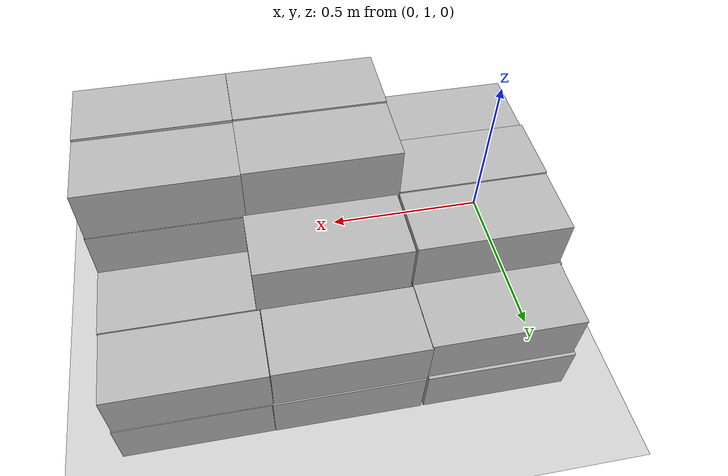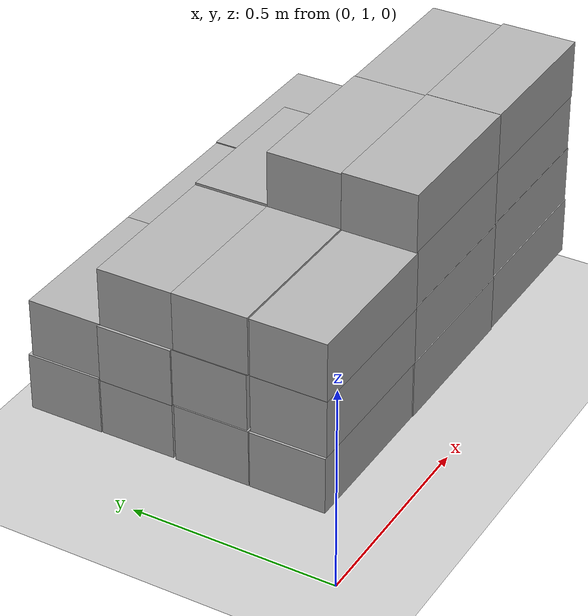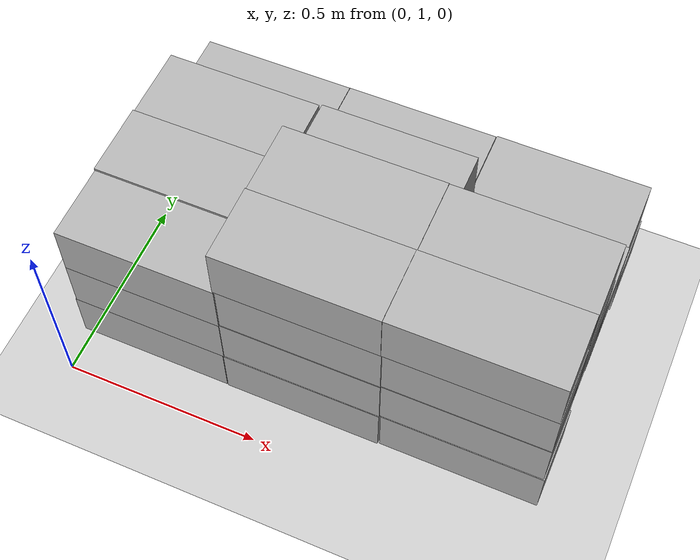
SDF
<sdf version="1.7">
 <world name="default">
  <light name="sun" type="directional">
   <pose>0 0 10 0 -0 0</pose>
   <diffuse>0.8 0.8 0.8 1</diffuse>
   <specular>0.2 0.2 0.2 1</specular>
   <attenuation>
    <range>1000</range>
    <constant>0.9</constant>
    <linear>0.01</linear>
    <quadratic>0.001</quadratic>
   </attenuation>
   <direction>-0.5 0.1 -0.9</direction>
   <spot><inner_angle>0</inner_angle><outer_angle>0</outer_angle><falloff>0</falloff></spot>
  </light>
  <model name="ground_plane">
   <static>1</static>
   <link name="link">
    <collision name="collision">
     <geometry><plane><normal>0 0 1</normal><size>100 100</size></plane></geometry>
     <surface>
      <contact><collide_bitmask>65535</collide_bitmask></contact>
      <friction><ode><mu>100</mu><mu2>50</mu2></ode></friction>
     </surface>
    </collision>
    <visual name="visual">
     <cast_shadows>0</cast_shadows>
     <geometry><plane><normal>0 0 1</normal><size>100 100</size></plane></geometry>
     <material>
      <script><uri>file://media/materials/scripts/gazebo.material</uri><name>Gazebo/Gray</name></script>
     </material>
    </visual>
   </link>
  </model>
  <gravity>0 0 -9.8</gravity>
  <magnetic_field>6e-06 2.3e-05 -4.2e-05</magnetic_field>
  <atmosphere type="adiabatic"/>
  <physics type="ode">
   <max_step_size>0.001</max_step_size>
   <real_time_factor>1</real_time_factor>
   <real_time_update_rate>1000</real_time_update_rate>
  </physics>
  <scene><ambient>0.4 0.4 0.4 1</ambient><background>0.7 0.7 0.7 1</background><shadows>1</shadows></scene>
  <spherical_coordinates>
   <surface_model>EARTH_WGS84</surface_model>
   <latitude_deg>0</latitude_deg>
   <longitude_deg>0</longitude_deg>
   <elevation>0</elevation>
   <heading_deg>0</heading_deg>
  </spherical_coordinates>
  <model name="box_38_18_14">
   <link name="link_0">
    <inertial>
     <mass>2.5</mass>
     <inertia>
      <ixx>0.0108332</ixx>
      <ixy>0</ixy>
      <ixz>0</ixz>
      <iyy>0.0341665</iyy>
      <iyz>0</iyz>
      <izz>0.0368332</izz>
     </inertia>
    </inertial>
    <visual name="visual">
     <geometry><box><size>0.38 0.18 0.14</size></box></geometry>
     <material>
      <lighting>1</lighting>
      <script><uri>file://media/materials/scripts/cardpaper.material</uri><name>cardpaper</name></script>
      <shader type="pixel"><normal_map>__default__</normal_map></shader>
      <ambient>0.3 0.3 0.3 1</ambient>
      <diffuse>0.7 0.7 0.7 1</diffuse>
      <specular>0.01 0.01 0.01 1</specular>
      <emissive>0 0 0 1</emissive>
     </material>
    </visual>
    <collision name="collision">
     <geometry><box><size>0.38 0.18 0.14</size></box></geometry>
     <surface>
      <friction>
       <ode><mu>0.6</mu><mu2>0.6</mu2><fdir1>0 0 0</fdir1><slip1>0</slip1><slip2>0</slip2></ode>
       <torsional>
        <coefficient>1</coefficient>
        <patch_radius>0</patch_radius>
        <surface_radius>0</surface_radius>
        <use_patch_radius>1</use_patch_radius>
        <ode><slip>0</slip></ode>
       </torsional>
      </friction>
      <bounce><restitution_coefficient>0</restitution_coefficient><threshold>1e+06</threshold></bounce>
      <contact>
       <collide_without_contact>0</collide_without_contact>
       <collide_without_contact_bitmask>1</collide_without_contact_bitmask>
       <collide_bitmask>1</collide_bitmask>
       <ode>
        <soft_cfm>0</soft_cfm>
        <soft_erp>0.2</soft_erp>
        <kp>1e+13</kp>
        <kd>1</kd>
        <max_vel>0.01</max_vel>
        <min_depth>0.01</min_depth>
       </ode>
       <bullet>
        <split_impulse>1</split_impulse>
        <split_impulse_penetration_threshold>-0.01</split_impulse_penetration_threshold>
        <soft_cfm>0</soft_cfm>
        <soft_erp>0.2</soft_erp>
        <kp>1e+13</kp>
        <kd>1</kd>
       </bullet>
      </contact>
     </surface>
    </collision>
   </link>
   <static>0</static>
   <pose>0.990718 1.14029 0.63626 0.000484 0.001138 0.001894</pose>
  </model>
  <model name="box_38_18_14_0">
   <link name="link_0">
    <inertial>
     <mass>2.5</mass>
     <inertia>
      <ixx>0.0108332</ixx>
      <ixy>0</ixy>
      <ixz>0</ixz>
      <iyy>0.0341665</iyy>
      <iyz>0</iyz>
      <izz>0.0368332</izz>
     </inertia>
    </inertial>
    <visual name="visual">
     <geometry><box><size>0.38 0.18 0.14</size></box></geometry>
     <material>
      <lighting>1</lighting>
      <script><uri>file://media/materials/scripts/cardpaper.material</uri><name>cardpaper</name></script>
      <shader type="pixel"><normal_map>__default__</normal_map></shader>
      <ambient>0.3 0.3 0.3 1</ambient>
      <diffuse>0.7 0.7 0.7 1</diffuse>
      <specular>0.01 0.01 0.01 1</specular>
      <emissive>0 0 0 1</emissive>
     </material>
    </visual>
    <collision name="collision">
     <geometry><box><size>0.38 0.18 0.14</size></box></geometry>
     <surface>
      <friction>
       <ode><mu>0.6</mu><mu2>0.6</mu2><fdir1>0 0 0</fdir1><slip1>0</slip1><slip2>0</slip2></ode>
       <torsional>
        <coefficient>1</coefficient>
        <patch_radius>0</patch_radius>
        <surface_radius>0</surface_radius>
        <use_patch_radius>1</use_patch_radius>
        <ode><slip>0</slip></ode>
       </torsional>
      </friction>
      <bounce><restitution_coefficient>0</restitution_coefficient><threshold>1e+06</threshold></bounce>
      <contact>
       <collide_without_contact>0</collide_without_contact>
       <collide_without_contact_bitmask>1</collide_without_contact_bitmask>
       <collide_bitmask>1</collide_bitmask>
       <ode>
        <soft_cfm>0</soft_cfm>
        <soft_erp>0.2</soft_erp>
        <kp>1e+13</kp>
        <kd>1</kd>
        <max_vel>0.01</max_vel>
        <min_depth>0.01</min_depth>
       </ode>
       <bullet>
        <split_impulse>1</split_impulse>
        <split_impulse_penetration_threshold>-0.01</split_impulse_penetration_threshold>
        <soft_cfm>0</soft_cfm>
        <soft_erp>0.2</soft_erp>
        <kp>1e+13</kp>
        <kd>1</kd>
       </bullet>
      </contact>
     </surface>
    </collision>
   </link>
   <static>0</static>
   <pose>0.610379 1.13953 0.636527 0.0002 0.000296 0.000292</pose>
  </model>
  <model name="box_38_18_14_1">
   <link name="link_0">
    <inertial>
     <mass>2.5</mass>
     <inertia>
      <ixx>0.0108332</ixx>
      <ixy>0</ixy>
      <ixz>0</ixz>
      <iyy>0.0341665</iyy>
      <iyz>0</iyz>
      <izz>0.0368332</izz>
     </inertia>
    </inertial>
    <visual name="visual">
     <geometry><box><size>0.38 0.18 0.14</size></box></geometry>
     <material>
      <lighting>1</lighting>
      <script><uri>file://media/materials/scripts/cardpaper.material</uri><name>cardpaper</name></script>
      <shader type="pixel"><normal_map>__default__</normal_map></shader>
      <ambient>0.3 0.3 0.3 1</ambient>
      <diffuse>0.7 0.7 0.7 1</diffuse>
      <specular>0.01 0.01 0.01 1</specular>
      <emissive>0 0 0 1</emissive>
     </material>
    </visual>
    <collision name="collision">
     <geometry><box><size>0.38 0.18 0.14</size></box></geometry>
     <surface>
      <friction>
       <ode><mu>0.6</mu><mu2>0.6</mu2><fdir1>0 0 0</fdir1><slip1>0</slip1><slip2>0</slip2></ode>
       <torsional>
        <coefficient>1</coefficient>
        <patch_radius>0</patch_radius>
        <surface_radius>0</surface_radius>
        <use_patch_radius>1</use_patch_radius>
        <ode><slip>0</slip></ode>
       </torsional>
      </friction>
      <bounce><restitution_coefficient>0</restitution_coefficient><threshold>1e+06</threshold></bounce>
      <contact>
       <collide_without_contact>0</collide_without_contact>
       <collide_without_contact_bitmask>1</collide_without_contact_bitmask>
       <collide_bitmask>1</collide_bitmask>
       <ode>
        <soft_cfm>0</soft_cfm>
        <soft_erp>0.2</soft_erp>
        <kp>1e+13</kp>
        <kd>1</kd>
        <max_vel>0.01</max_vel>
        <min_depth>0.01</min_depth>
       </ode>
       <bullet>
        <split_impulse>1</split_impulse>
        <split_impulse_penetration_threshold>-0.01</split_impulse_penetration_threshold>
        <soft_cfm>0</soft_cfm>
        <soft_erp>0.2</soft_erp>
        <kp>1e+13</kp>
        <kd>1</kd>
       </bullet>
      </contact>
     </surface>
    </collision>
   </link>
   <static>1</static>
   <pose>0.995594 1.14055 0.215337 -2.4e-05 -3.2e-05 -0.000547</pose>
  </model>
  <model name="box_38_18_14_2">
   <link name="link_0">
    <inertial>
     <mass>2.5</mass>
     <inertia>
      <ixx>0.0108332</ixx>
      <ixy>0</ixy>
      <ixz>0</ixz>
      <iyy>0.0341665</iyy>
      <iyz>0</iyz>
      <izz>0.0368332</izz>
     </inertia>
    </inertial>
    <visual name="visual">
     <geometry><box><size>0.38 0.18 0.14</size></box></geometry>
     <material>
      <lighting>1</lighting>
      <script><uri>file://media/materials/scripts/cardpaper.material</uri><name>cardpaper</name></script>
      <shader type="pixel"><normal_map>__default__</normal_map></shader>
      <ambient>0.3 0.3 0.3 1</ambient>
      <diffuse>0.7 0.7 0.7 1</diffuse>
      <specular>0.01 0.01 0.01 1</specular>
      <emissive>0 0 0 1</emissive>
     </material>
    </visual>
    <collision name="collision">
     <geometry><box><size>0.38 0.18 0.14</size></box></geometry>
     <surface>
      <friction>
       <ode><mu>0.6</mu><mu2>0.6</mu2><fdir1>0 0 0</fdir1><slip1>0</slip1><slip2>0</slip2></ode>
       <torsional>
        <coefficient>1</coefficient>
        <patch_radius>0</patch_radius>
        <surface_radius>0</surface_radius>
        <use_patch_radius>1</use_patch_radius>
        <ode><slip>0</slip></ode>
       </torsional>
      </friction>
      <bounce><restitution_coefficient>0</restitution_coefficient><threshold>1e+06</threshold></bounce>
      <contact>
       <collide_without_contact>0</collide_without_contact>
       <collide_without_contact_bitmask>1</collide_without_contact_bitmask>
       <collide_bitmask>1</collide_bitmask>
       <ode>
        <soft_cfm>0</soft_cfm>
        <soft_erp>0.2</soft_erp>
        <kp>1e+13</kp>
        <kd>1</kd>
        <max_vel>0.01</max_vel>
        <min_depth>0.01</min_depth>
       </ode>
       <bullet>
        <split_impulse>1</split_impulse>
        <split_impulse_penetration_threshold>-0.01</split_impulse_penetration_threshold>
        <soft_cfm>0</soft_cfm>
        <soft_erp>0.2</soft_erp>
        <kp>1e+13</kp>
        <kd>1</kd>
       </bullet>
      </contact>
     </surface>
    </collision>
   </link>
   <static>1</static>
   <pose>0.61176 1.13834 0.214923 3.5e-05 -1.8e-05 0.000435</pose>
  </model>
  <model name="box_38_18_14_3">
   <link name="link_0">
    <inertial>
     <mass>2.5</mass>
     <inertia>
      <ixx>0.0108332</ixx>
      <ixy>0</ixy>
      <ixz>0</ixz>
      <iyy>0.0341665</iyy>
      <iyz>0</iyz>
      <izz>0.0368332</izz>
     </inertia>
    </inertial>
    <visual name="visual">
     <geometry><box><size>0.38 0.18 0.14</size></box></geometry>
     <material>
      <lighting>1</lighting>
      <script><uri>file://media/materials/scripts/cardpaper.material</uri><name>cardpaper</name></script>
      <shader type="pixel"><normal_map>__default__</normal_map></shader>
      <ambient>0.3 0.3 0.3 1</ambient>
      <diffuse>0.7 0.7 0.7 1</diffuse>
      <specular>0.01 0.01 0.01 1</specular>
      <emissive>0 0 0 1</emissive>
     </material>
    </visual>
    <collision name="collision">
     <geometry><box><size>0.38 0.18 0.14</size></box></geometry>
     <surface>
      <friction>
       <ode><mu>0.6</mu><mu2>0.6</mu2><fdir1>0 0 0</fdir1><slip1>0</slip1><slip2>0</slip2></ode>
       <torsional>
        <coefficient>1</coefficient>
        <patch_radius>0</patch_radius>
        <surface_radius>0</surface_radius>
        <use_patch_radius>1</use_patch_radius>
        <ode><slip>0</slip></ode>
       </torsional>
      </friction>
      <bounce><restitution_coefficient>0</restitution_coefficient><threshold>1e+06</threshold></bounce>
      <contact>
       <collide_without_contact>0</collide_without_contact>
       <collide_without_contact_bitmask>1</collide_without_contact_bitmask>
       <collide_bitmask>1</collide_bitmask>
       <ode>
        <soft_cfm>0</soft_cfm>
        <soft_erp>0.2</soft_erp>
        <kp>1e+13</kp>
        <kd>1</kd>
        <max_vel>0.01</max_vel>
        <min_depth>0.01</min_depth>
       </ode>
       <bullet>
        <split_impulse>1</split_impulse>
        <split_impulse_penetration_threshold>-0.01</split_impulse_penetration_threshold>
        <soft_cfm>0</soft_cfm>
        <soft_erp>0.2</soft_erp>
        <kp>1e+13</kp>
        <kd>1</kd>
       </bullet>
      </contact>
     </surface>
    </collision>
   </link>
   <static>1</static>
   <pose>0.229172 1.13951 0.215224 2.7e-05 -2e-05 5e-06</pose>
  </model>
  <model name="box_38_18_14_4">
   <link name="link_0">
    <inertial>
     <mass>2.5</mass>
     <inertia>
      <ixx>0.0108332</ixx>
      <ixy>0</ixy>
      <ixz>0</ixz>
      <iyy>0.0341665</iyy>
      <iyz>0</iyz>
      <izz>0.0368332</izz>
     </inertia>
    </inertial>
    <visual name="visual">
     <geometry><box><size>0.38 0.18 0.14</size></box></geometry>
     <material>
      <lighting>1</lighting>
      <script><uri>file://media/materials/scripts/cardpaper.material</uri><name>cardpaper</name></script>
      <shader type="pixel"><normal_map>__default__</normal_map></shader>
      <ambient>0.3 0.3 0.3 1</ambient>
      <diffuse>0.7 0.7 0.7 1</diffuse>
      <specular>0.01 0.01 0.01 1</specular>
      <emissive>0 0 0 1</emissive>
     </material>
    </visual>
    <collision name="collision">
     <geometry><box><size>0.38 0.18 0.14</size></box></geometry>
     <surface>
      <friction>
       <ode><mu>0.6</mu><mu2>0.6</mu2><fdir1>0 0 0</fdir1><slip1>0</slip1><slip2>0</slip2></ode>
       <torsional>
        <coefficient>1</coefficient>
        <patch_radius>0</patch_radius>
        <surface_radius>0</surface_radius>
        <use_patch_radius>1</use_patch_radius>
        <ode><slip>0</slip></ode>
       </torsional>
      </friction>
      <bounce><restitution_coefficient>0</restitution_coefficient><threshold>1e+06</threshold></bounce>
      <contact>
       <collide_without_contact>0</collide_without_contact>
       <collide_without_contact_bitmask>1</collide_without_contact_bitmask>
       <collide_bitmask>1</collide_bitmask>
       <ode>
        <soft_cfm>0</soft_cfm>
        <soft_erp>0.2</soft_erp>
        <kp>1e+13</kp>
        <kd>1</kd>
        <max_vel>0.01</max_vel>
        <min_depth>0.01</min_depth>
       </ode>
       <bullet>
        <split_impulse>1</split_impulse>
        <split_impulse_penetration_threshold>-0.01</split_impulse_penetration_threshold>
        <soft_cfm>0</soft_cfm>
        <soft_erp>0.2</soft_erp>
        <kp>1e+13</kp>
        <kd>1</kd>
       </bullet>
      </contact>
     </surface>
    </collision>
   </link>
   <static>1</static>
   <pose>0.98709 1.3217 0.21457 -2.4e-05 -1.9e-05 -1.8e-05</pose>
  </model>
  <model name="box_38_18_14_5">
   <link name="link_0">
    <inertial>
     <mass>2.5</mass>
     <inertia>
      <ixx>0.0108332</ixx>
      <ixy>0</ixy>
      <ixz>0</ixz>
      <iyy>0.0341665</iyy>
      <iyz>0</iyz>
      <izz>0.0368332</izz>
     </inertia>
    </inertial>
    <visual name="visual">
     <geometry><box><size>0.38 0.18 0.14</size></box></geometry>
     <material>
      <lighting>1</lighting>
      <script><uri>file://media/materials/scripts/cardpaper.material</uri><name>cardpaper</name></script>
      <shader type="pixel"><normal_map>__default__</normal_map></shader>
      <ambient>0.3 0.3 0.3 1</ambient>
      <diffuse>0.7 0.7 0.7 1</diffuse>
      <specular>0.01 0.01 0.01 1</specular>
      <emissive>0 0 0 1</emissive>
     </material>
    </visual>
    <collision name="collision">
     <geometry><box><size>0.38 0.18 0.14</size></box></geometry>
     <surface>
      <friction>
       <ode><mu>0.6</mu><mu2>0.6</mu2><fdir1>0 0 0</fdir1><slip1>0</slip1><slip2>0</slip2></ode>
       <torsional>
        <coefficient>1</coefficient>
        <patch_radius>0</patch_radius>
        <surface_radius>0</surface_radius>
        <use_patch_radius>1</use_patch_radius>
        <ode><slip>0</slip></ode>
       </torsional>
      </friction>
      <bounce><restitution_coefficient>0</restitution_coefficient><threshold>1e+06</threshold></bounce>
      <contact>
       <collide_without_contact>0</collide_without_contact>
       <collide_without_contact_bitmask>1</collide_without_contact_bitmask>
       <collide_bitmask>1</collide_bitmask>
       <ode>
        <soft_cfm>0</soft_cfm>
        <soft_erp>0.2</soft_erp>
        <kp>1e+13</kp>
        <kd>1</kd>
        <max_vel>0.01</max_vel>
        <min_depth>0.01</min_depth>
       </ode>
       <bullet>
        <split_impulse>1</split_impulse>
        <split_impulse_penetration_threshold>-0.01</split_impulse_penetration_threshold>
        <soft_cfm>0</soft_cfm>
        <soft_erp>0.2</soft_erp>
        <kp>1e+13</kp>
        <kd>1</kd>
       </bullet>
      </contact>
     </surface>
    </collision>
   </link>
   <static>1</static>
   <pose>0.61137 1.32116 0.191996 -1e-06 -2.4e-05 -0.000217</pose>
  </model>
  <model name="box_38_18_14_6">
   <link name="link_0">
    <inertial>
     <mass>2.5</mass>
     <inertia>
      <ixx>0.0108332</ixx>
      <ixy>0</ixy>
      <ixz>0</ixz>
      <iyy>0.0341665</iyy>
      <iyz>0</iyz>
      <izz>0.0368332</izz>
     </inertia>
    </inertial>
    <visual name="visual">
     <geometry><box><size>0.38 0.18 0.14</size></box></geometry>
     <material>
      <lighting>1</lighting>
      <script><uri>file://media/materials/scripts/cardpaper.material</uri><name>cardpaper</name></script>
      <shader type="pixel"><normal_map>__default__</normal_map></shader>
      <ambient>0.3 0.3 0.3 1</ambient>
      <diffuse>0.7 0.7 0.7 1</diffuse>
      <specular>0.01 0.01 0.01 1</specular>
      <emissive>0 0 0 1</emissive>
     </material>
    </visual>
    <collision name="collision">
     <geometry><box><size>0.38 0.18 0.14</size></box></geometry>
     <surface>
      <friction>
       <ode><mu>0.6</mu><mu2>0.6</mu2><fdir1>0 0 0</fdir1><slip1>0</slip1><slip2>0</slip2></ode>
       <torsional>
        <coefficient>1</coefficient>
        <patch_radius>0</patch_radius>
        <surface_radius>0</surface_radius>
        <use_patch_radius>1</use_patch_radius>
        <ode><slip>0</slip></ode>
       </torsional>
      </friction>
      <bounce><restitution_coefficient>0</restitution_coefficient><threshold>1e+06</threshold></bounce>
      <contact>
       <collide_without_contact>0</collide_without_contact>
       <collide_without_contact_bitmask>1</collide_without_contact_bitmask>
       <collide_bitmask>1</collide_bitmask>
       <ode>
        <soft_cfm>0</soft_cfm>
        <soft_erp>0.2</soft_erp>
        <kp>1e+13</kp>
        <kd>1</kd>
        <max_vel>0.01</max_vel>
        <min_depth>0.01</min_depth>
       </ode>
       <bullet>
        <split_impulse>1</split_impulse>
        <split_impulse_penetration_threshold>-0.01</split_impulse_penetration_threshold>
        <soft_cfm>0</soft_cfm>
        <soft_erp>0.2</soft_erp>
        <kp>1e+13</kp>
        <kd>1</kd>
       </bullet>
      </contact>
     </surface>
    </collision>
   </link>
   <static>1</static>
   <pose>0.228982 1.32157 0.215841 2.7e-05 -2.1e-05 0.000396</pose>
  </model>
  <model name="box_38_18_14_7">
   <link name="link_0">
    <inertial>
     <mass>2.5</mass>
     <inertia>
      <ixx>0.0108332</ixx>
      <ixy>0</ixy>
      <ixz>0</ixz>
      <iyy>0.0341665</iyy>
      <iyz>0</iyz>
      <izz>0.0368332</izz>
     </inertia>
    </inertial>
    <visual name="visual">
     <geometry><box><size>0.38 0.18 0.14</size></box></geometry>
     <material>
      <lighting>1</lighting>
      <script><uri>file://media/materials/scripts/cardpaper.material</uri><name>cardpaper</name></script>
      <shader type="pixel"><normal_map>__default__</normal_map></shader>
      <ambient>0.3 0.3 0.3 1</ambient>
      <diffuse>0.7 0.7 0.7 1</diffuse>
      <specular>0.01 0.01 0.01 1</specular>
      <emissive>0 0 0 1</emissive>
     </material>
    </visual>
    <collision name="collision">
     <geometry><box><size>0.38 0.18 0.14</size></box></geometry>
     <surface>
      <friction>
       <ode><mu>0.6</mu><mu2>0.6</mu2><fdir1>0 0 0</fdir1><slip1>0</slip1><slip2>0</slip2></ode>
       <torsional>
        <coefficient>1</coefficient>
        <patch_radius>0</patch_radius>
        <surface_radius>0</surface_radius>
        <use_patch_radius>1</use_patch_radius>
        <ode><slip>0</slip></ode>
       </torsional>
      </friction>
      <bounce><restitution_coefficient>0</restitution_coefficient><threshold>1e+06</threshold></bounce>
      <contact>
       <collide_without_contact>0</collide_without_contact>
       <collide_without_contact_bitmask>1</collide_without_contact_bitmask>
       <collide_bitmask>1</collide_bitmask>
       <ode>
        <soft_cfm>0</soft_cfm>
        <soft_erp>0.2</soft_erp>
        <kp>1e+13</kp>
        <kd>1</kd>
        <max_vel>0.01</max_vel>
        <min_depth>0.01</min_depth>
       </ode>
       <bullet>
        <split_impulse>1</split_impulse>
        <split_impulse_penetration_threshold>-0.01</split_impulse_penetration_threshold>
        <soft_cfm>0</soft_cfm>
        <soft_erp>0.2</soft_erp>
        <kp>1e+13</kp>
        <kd>1</kd>
       </bullet>
      </contact>
     </surface>
    </collision>
   </link>
   <static>1</static>
   <pose>0.990184 1.50391 0.216547 2.8e-05 -2e-05 -0.000315</pose>
  </model>
  <model name="box_38_18_14_8">
   <link name="link_0">
    <inertial>
     <mass>2.5</mass>
     <inertia>
      <ixx>0.0108332</ixx>
      <ixy>0</ixy>
      <ixz>0</ixz>
      <iyy>0.0341665</iyy>
      <iyz>0</iyz>
      <izz>0.0368332</izz>
     </inertia>
    </inertial>
    <visual name="visual">
     <geometry><box><size>0.38 0.18 0.14</size></box></geometry>
     <material>
      <lighting>1</lighting>
      <script><uri>file://media/materials/scripts/cardpaper.material</uri><name>cardpaper</name></script>
      <shader type="pixel"><normal_map>__default__</normal_map></shader>
      <ambient>0.3 0.3 0.3 1</ambient>
      <diffuse>0.7 0.7 0.7 1</diffuse>
      <specular>0.01 0.01 0.01 1</specular>
      <emissive>0 0 0 1</emissive>
     </material>
    </visual>
    <collision name="collision">
     <geometry><box><size>0.38 0.18 0.14</size></box></geometry>
     <surface>
      <friction>
       <ode><mu>0.6</mu><mu2>0.6</mu2><fdir1>0 0 0</fdir1><slip1>0</slip1><slip2>0</slip2></ode>
       <torsional>
        <coefficient>1</coefficient>
        <patch_radius>0</patch_radius>
        <surface_radius>0</surface_radius>
        <use_patch_radius>1</use_patch_radius>
        <ode><slip>0</slip></ode>
       </torsional>
      </friction>
      <bounce><restitution_coefficient>0</restitution_coefficient><threshold>1e+06</threshold></bounce>
      <contact>
       <collide_without_contact>0</collide_without_contact>
       <collide_without_contact_bitmask>1</collide_without_contact_bitmask>
       <collide_bitmask>1</collide_bitmask>
       <ode>
        <soft_cfm>0</soft_cfm>
        <soft_erp>0.2</soft_erp>
        <kp>1e+13</kp>
        <kd>1</kd>
        <max_vel>0.01</max_vel>
        <min_depth>0.01</min_depth>
       </ode>
       <bullet>
        <split_impulse>1</split_impulse>
        <split_impulse_penetration_threshold>-0.01</split_impulse_penetration_threshold>
        <soft_cfm>0</soft_cfm>
        <soft_erp>0.2</soft_erp>
        <kp>1e+13</kp>
        <kd>1</kd>
       </bullet>
      </contact>
     </surface>
    </collision>
   </link>
   <static>1</static>
   <pose>0.611731 1.50421 0.192002 2.6e-05 -2e-05 -3.2e-05</pose>
  </model>
  <model name="box_38_18_14_9">
   <link name="link_0">
    <inertial>
     <mass>2.5</mass>
     <inertia>
      <ixx>0.0108332</ixx>
      <ixy>0</ixy>
      <ixz>0</ixz>
      <iyy>0.0341665</iyy>
      <iyz>0</iyz>
      <izz>0.0368332</izz>
     </inertia>
    </inertial>
    <visual name="visual">
     <geometry><box><size>0.38 0.18 0.14</size></box></geometry>
     <material>
      <lighting>1</lighting>
      <script><uri>file://media/materials/scripts/cardpaper.material</uri><name>cardpaper</name></script>
      <shader type="pixel"><normal_map>__default__</normal_map></shader>
      <ambient>0.3 0.3 0.3 1</ambient>
      <diffuse>0.7 0.7 0.7 1</diffuse>
      <specular>0.01 0.01 0.01 1</specular>
      <emissive>0 0 0 1</emissive>
     </material>
    </visual>
    <collision name="collision">
     <geometry><box><size>0.38 0.18 0.14</size></box></geometry>
     <surface>
      <friction>
       <ode><mu>0.6</mu><mu2>0.6</mu2><fdir1>0 0 0</fdir1><slip1>0</slip1><slip2>0</slip2></ode>
       <torsional>
        <coefficient>1</coefficient>
        <patch_radius>0</patch_radius>
        <surface_radius>0</surface_radius>
        <use_patch_radius>1</use_patch_radius>
        <ode><slip>0</slip></ode>
       </torsional>
      </friction>
      <bounce><restitution_coefficient>0</restitution_coefficient><threshold>1e+06</threshold></bounce>
      <contact>
       <collide_without_contact>0</collide_without_contact>
       <collide_without_contact_bitmask>1</collide_without_contact_bitmask>
       <collide_bitmask>1</collide_bitmask>
       <ode>
        <soft_cfm>0</soft_cfm>
        <soft_erp>0.2</soft_erp>
        <kp>1e+13</kp>
        <kd>1</kd>
        <max_vel>0.01</max_vel>
        <min_depth>0.01</min_depth>
       </ode>
       <bullet>
        <split_impulse>1</split_impulse>
        <split_impulse_penetration_threshold>-0.01</split_impulse_penetration_threshold>
        <soft_cfm>0</soft_cfm>
        <soft_erp>0.2</soft_erp>
        <kp>1e+13</kp>
        <kd>1</kd>
       </bullet>
      </contact>
     </surface>
    </collision>
   </link>
   <static>1</static>
   <pose>0.228512 1.50611 0.218021 2.9e-05 -2e-05 0.000472</pose>
  </model>
  <model name="box_38_18_14_10">
   <link name="link_0">
    <inertial>
     <mass>2.5</mass>
     <inertia>
      <ixx>0.0108332</ixx>
      <ixy>0</ixy>
      <ixz>0</ixz>
      <iyy>0.0341665</iyy>
      <iyz>0</iyz>
      <izz>0.0368332</izz>
     </inertia>
    </inertial>
    <visual name="visual">
     <geometry><box><size>0.38 0.18 0.14</size></box></geometry>
     <material>
      <lighting>1</lighting>
      <script><uri>file://media/materials/scripts/cardpaper.material</uri><name>cardpaper</name></script>
      <shader type="pixel"><normal_map>__default__</normal_map></shader>
      <ambient>0.3 0.3 0.3 1</ambient>
      <diffuse>0.7 0.7 0.7 1</diffuse>
      <specular>0.01 0.01 0.01 1</specular>
      <emissive>0 0 0 1</emissive>
     </material>
    </visual>
    <collision name="collision">
     <geometry><box><size>0.38 0.18 0.14</size></box></geometry>
     <surface>
      <friction>
       <ode><mu>0.6</mu><mu2>0.6</mu2><fdir1>0 0 0</fdir1><slip1>0</slip1><slip2>0</slip2></ode>
       <torsional>
        <coefficient>1</coefficient>
        <patch_radius>0</patch_radius>
        <surface_radius>0</surface_radius>
        <use_patch_radius>1</use_patch_radius>
        <ode><slip>0</slip></ode>
       </torsional>
      </friction>
      <bounce><restitution_coefficient>0</restitution_coefficient><threshold>1e+06</threshold></bounce>
      <contact>
       <collide_without_contact>0</collide_without_contact>
       <collide_without_contact_bitmask>1</collide_without_contact_bitmask>
       <collide_bitmask>1</collide_bitmask>
       <ode>
        <soft_cfm>0</soft_cfm>
        <soft_erp>0.2</soft_erp>
        <kp>1e+13</kp>
        <kd>1</kd>
        <max_vel>0.01</max_vel>
        <min_depth>0.01</min_depth>
       </ode>
       <bullet>
        <split_impulse>1</split_impulse>
        <split_impulse_penetration_threshold>-0.01</split_impulse_penetration_threshold>
        <soft_cfm>0</soft_cfm>
        <soft_erp>0.2</soft_erp>
        <kp>1e+13</kp>
        <kd>1</kd>
       </bullet>
      </contact>
     </surface>
    </collision>
   </link>
   <static>1</static>
   <pose>0.993831 1.68679 0.217454 2.6e-05 -2e-05 0.000237</pose>
  </model>
  <model name="box_38_18_14_11">
   <link name="link_0">
    <inertial>
     <mass>2.5</mass>
     <inertia>
      <ixx>0.0108332</ixx>
      <ixy>0</ixy>
      <ixz>0</ixz>
      <iyy>0.0341665</iyy>
      <iyz>0</iyz>
      <izz>0.0368332</izz>
     </inertia>
    </inertial>
    <visual name="visual">
     <geometry><box><size>0.38 0.18 0.14</size></box></geometry>
     <material>
      <lighting>1</lighting>
      <script><uri>file://media/materials/scripts/cardpaper.material</uri><name>cardpaper</name></script>
      <shader type="pixel"><normal_map>__default__</normal_map></shader>
      <ambient>0.3 0.3 0.3 1</ambient>
      <diffuse>0.7 0.7 0.7 1</diffuse>
      <specular>0.01 0.01 0.01 1</specular>
      <emissive>0 0 0 1</emissive>
     </material>
    </visual>
    <collision name="collision">
     <geometry><box><size>0.38 0.18 0.14</size></box></geometry>
     <surface>
      <friction>
       <ode><mu>0.6</mu><mu2>0.6</mu2><fdir1>0 0 0</fdir1><slip1>0</slip1><slip2>0</slip2></ode>
       <torsional>
        <coefficient>1</coefficient>
        <patch_radius>0</patch_radius>
        <surface_radius>0</surface_radius>
        <use_patch_radius>1</use_patch_radius>
        <ode><slip>0</slip></ode>
       </torsional>
      </friction>
      <bounce><restitution_coefficient>0</restitution_coefficient><threshold>1e+06</threshold></bounce>
      <contact>
       <collide_without_contact>0</collide_without_contact>
       <collide_without_contact_bitmask>1</collide_without_contact_bitmask>
       <collide_bitmask>1</collide_bitmask>
       <ode>
        <soft_cfm>0</soft_cfm>
        <soft_erp>0.2</soft_erp>
        <kp>1e+13</kp>
        <kd>1</kd>
        <max_vel>0.01</max_vel>
        <min_depth>0.01</min_depth>
       </ode>
       <bullet>
        <split_impulse>1</split_impulse>
        <split_impulse_penetration_threshold>-0.01</split_impulse_penetration_threshold>
        <soft_cfm>0</soft_cfm>
        <soft_erp>0.2</soft_erp>
        <kp>1e+13</kp>
        <kd>1</kd>
       </bullet>
      </contact>
     </surface>
    </collision>
   </link>
   <static>1</static>
   <pose>0.612289 1.68672 0.215492 2.9e-05 -2.3e-05 -0.001084</pose>
  </model>
  <model name="box_38_18_14_12">
   <link name="link_0">
    <inertial>
     <mass>2.5</mass>
     <inertia>
      <ixx>0.0108332</ixx>
      <ixy>0</ixy>
      <ixz>0</ixz>
      <iyy>0.0341665</iyy>
      <iyz>0</iyz>
      <izz>0.0368332</izz>
     </inertia>
    </inertial>
    <visual name="visual">
     <geometry><box><size>0.38 0.18 0.14</size></box></geometry>
     <material>
      <lighting>1</lighting>
      <script><uri>file://media/materials/scripts/cardpaper.material</uri><name>cardpaper</name></script>
      <shader type="pixel"><normal_map>__default__</normal_map></shader>
      <ambient>0.3 0.3 0.3 1</ambient>
      <diffuse>0.7 0.7 0.7 1</diffuse>
      <specular>0.01 0.01 0.01 1</specular>
      <emissive>0 0 0 1</emissive>
     </material>
    </visual>
    <collision name="collision">
     <geometry><box><size>0.38 0.18 0.14</size></box></geometry>
     <surface>
      <friction>
       <ode><mu>0.6</mu><mu2>0.6</mu2><fdir1>0 0 0</fdir1><slip1>0</slip1><slip2>0</slip2></ode>
       <torsional>
        <coefficient>1</coefficient>
        <patch_radius>0</patch_radius>
        <surface_radius>0</surface_radius>
        <use_patch_radius>1</use_patch_radius>
        <ode><slip>0</slip></ode>
       </torsional>
      </friction>
      <bounce><restitution_coefficient>0</restitution_coefficient><threshold>1e+06</threshold></bounce>
      <contact>
       <collide_without_contact>0</collide_without_contact>
       <collide_without_contact_bitmask>1</collide_without_contact_bitmask>
       <collide_bitmask>1</collide_bitmask>
       <ode>
        <soft_cfm>0</soft_cfm>
        <soft_erp>0.2</soft_erp>
        <kp>1e+13</kp>
        <kd>1</kd>
        <max_vel>0.01</max_vel>
        <min_depth>0.01</min_depth>
       </ode>
       <bullet>
        <split_impulse>1</split_impulse>
        <split_impulse_penetration_threshold>-0.01</split_impulse_penetration_threshold>
        <soft_cfm>0</soft_cfm>
        <soft_erp>0.2</soft_erp>
        <kp>1e+13</kp>
        <kd>1</kd>
       </bullet>
      </contact>
     </surface>
    </collision>
   </link>
   <static>1</static>
   <pose>0.226986 1.68817 0.218375 2.7e-05 -2.1e-05 0.000476</pose>
  </model>
  <model name="box_38_18_14_13">
   <link name="link_0">
    <inertial>
     <mass>2.5</mass>
     <inertia>
      <ixx>0.0108332</ixx>
      <ixy>0</ixy>
      <ixz>0</ixz>
      <iyy>0.0341665</iyy>
      <iyz>0</iyz>
      <izz>0.0368332</izz>
     </inertia>
    </inertial>
    <visual name="visual">
     <geometry><box><size>0.38 0.18 0.14</size></box></geometry>
     <material>
      <lighting>1</lighting>
      <script><uri>file://media/materials/scripts/cardpaper.material</uri><name>cardpaper</name></script>
      <shader type="pixel"><normal_map>__default__</normal_map></shader>
      <ambient>0.3 0.3 0.3 1</ambient>
      <diffuse>0.7 0.7 0.7 1</diffuse>
      <specular>0.01 0.01 0.01 1</specular>
      <emissive>0 0 0 1</emissive>
     </material>
    </visual>
    <collision name="collision">
     <geometry><box><size>0.38 0.18 0.14</size></box></geometry>
     <surface>
      <friction>
       <ode><mu>0.6</mu><mu2>0.6</mu2><fdir1>0 0 0</fdir1><slip1>0</slip1><slip2>0</slip2></ode>
       <torsional>
        <coefficient>1</coefficient>
        <patch_radius>0</patch_radius>
        <surface_radius>0</surface_radius>
        <use_patch_radius>1</use_patch_radius>
        <ode><slip>0</slip></ode>
       </torsional>
      </friction>
      <bounce><restitution_coefficient>0</restitution_coefficient><threshold>1e+06</threshold></bounce>
      <contact>
       <collide_without_contact>0</collide_without_contact>
       <collide_without_contact_bitmask>1</collide_without_contact_bitmask>
       <collide_bitmask>1</collide_bitmask>
       <ode>
        <soft_cfm>0</soft_cfm>
        <soft_erp>0.2</soft_erp>
        <kp>1e+13</kp>
        <kd>1</kd>
        <max_vel>0.01</max_vel>
        <min_depth>0.01</min_depth>
       </ode>
       <bullet>
        <split_impulse>1</split_impulse>
        <split_impulse_penetration_threshold>-0.01</split_impulse_penetration_threshold>
        <soft_cfm>0</soft_cfm>
        <soft_erp>0.2</soft_erp>
        <kp>1e+13</kp>
        <kd>1</kd>
       </bullet>
      </contact>
     </surface>
    </collision>
   </link>
   <static>1</static>
   <pose>0.99286 1.14146 0.357504 0.000539 -3.4e-05 7.4e-05</pose>
  </model>
  <model name="box_38_18_14_14">
   <link name="link_0">
    <inertial>
     <mass>2.5</mass>
     <inertia>
      <ixx>0.0108332</ixx>
      <ixy>0</ixy>
      <ixz>0</ixz>
      <iyy>0.0341665</iyy>
      <iyz>0</iyz>
      <izz>0.0368332</izz>
     </inertia>
    </inertial>
    <visual name="visual">
     <geometry><box><size>0.38 0.18 0.14</size></box></geometry>
     <material>
      <lighting>1</lighting>
      <script><uri>file://media/materials/scripts/cardpaper.material</uri><name>cardpaper</name></script>
      <shader type="pixel"><normal_map>__default__</normal_map></shader>
      <ambient>0.3 0.3 0.3 1</ambient>
      <diffuse>0.7 0.7 0.7 1</diffuse>
      <specular>0.01 0.01 0.01 1</specular>
      <emissive>0 0 0 1</emissive>
     </material>
    </visual>
    <collision name="collision">
     <geometry><box><size>0.38 0.18 0.14</size></box></geometry>
     <surface>
      <friction>
       <ode><mu>0.6</mu><mu2>0.6</mu2><fdir1>0 0 0</fdir1><slip1>0</slip1><slip2>0</slip2></ode>
       <torsional>
        <coefficient>1</coefficient>
        <patch_radius>0</patch_radius>
        <surface_radius>0</surface_radius>
        <use_patch_radius>1</use_patch_radius>
        <ode><slip>0</slip></ode>
       </torsional>
      </friction>
      <bounce><restitution_coefficient>0</restitution_coefficient><threshold>1e+06</threshold></bounce>
      <contact>
       <collide_without_contact>0</collide_without_contact>
       <collide_without_contact_bitmask>1</collide_without_contact_bitmask>
       <collide_bitmask>1</collide_bitmask>
       <ode>
        <soft_cfm>0</soft_cfm>
        <soft_erp>0.2</soft_erp>
        <kp>1e+13</kp>
        <kd>1</kd>
        <max_vel>0.01</max_vel>
        <min_depth>0.01</min_depth>
       </ode>
       <bullet>
        <split_impulse>1</split_impulse>
        <split_impulse_penetration_threshold>-0.01</split_impulse_penetration_threshold>
        <soft_cfm>0</soft_cfm>
        <soft_erp>0.2</soft_erp>
        <kp>1e+13</kp>
        <kd>1</kd>
       </bullet>
      </contact>
     </surface>
    </collision>
   </link>
   <static>1</static>
   <pose>0.612101 1.13996 0.355387 0.000133 0.00021 -0.000244</pose>
  </model>
  <model name="box_38_18_14_15">
   <link name="link_0">
    <inertial>
     <mass>2.5</mass>
     <inertia>
      <ixx>0.0108332</ixx>
      <ixy>0</ixy>
      <ixz>0</ixz>
      <iyy>0.0341665</iyy>
      <iyz>0</iyz>
      <izz>0.0368332</izz>
     </inertia>
    </inertial>
    <visual name="visual">
     <geometry><box><size>0.38 0.18 0.14</size></box></geometry>
     <material>
      <lighting>1</lighting>
      <script><uri>file://media/materials/scripts/cardpaper.material</uri><name>cardpaper</name></script>
      <shader type="pixel"><normal_map>__default__</normal_map></shader>
      <ambient>0.3 0.3 0.3 1</ambient>
      <diffuse>0.7 0.7 0.7 1</diffuse>
      <specular>0.01 0.01 0.01 1</specular>
      <emissive>0 0 0 1</emissive>
     </material>
    </visual>
    <collision name="collision">
     <geometry><box><size>0.38 0.18 0.14</size></box></geometry>
     <surface>
      <friction>
       <ode><mu>0.6</mu><mu2>0.6</mu2><fdir1>0 0 0</fdir1><slip1>0</slip1><slip2>0</slip2></ode>
       <torsional>
        <coefficient>1</coefficient>
        <patch_radius>0</patch_radius>
        <surface_radius>0</surface_radius>
        <use_patch_radius>1</use_patch_radius>
        <ode><slip>0</slip></ode>
       </torsional>
      </friction>
      <bounce><restitution_coefficient>0</restitution_coefficient><threshold>1e+06</threshold></bounce>
      <contact>
       <collide_without_contact>0</collide_without_contact>
       <collide_without_contact_bitmask>1</collide_without_contact_bitmask>
       <collide_bitmask>1</collide_bitmask>
       <ode>
        <soft_cfm>0</soft_cfm>
        <soft_erp>0.2</soft_erp>
        <kp>1e+13</kp>
        <kd>1</kd>
        <max_vel>0.01</max_vel>
        <min_depth>0.01</min_depth>
       </ode>
       <bullet>
        <split_impulse>1</split_impulse>
        <split_impulse_penetration_threshold>-0.01</split_impulse_penetration_threshold>
        <soft_cfm>0</soft_cfm>
        <soft_erp>0.2</soft_erp>
        <kp>1e+13</kp>
        <kd>1</kd>
       </bullet>
      </contact>
     </surface>
    </collision>
   </link>
   <static>1</static>
   <pose>0.233033 1.13804 0.35663 3e-05 -6.7e-05 6.3e-05</pose>
  </model>
  <model name="box_38_18_14_16">
   <link name="link_0">
    <inertial>
     <mass>2.5</mass>
     <inertia>
      <ixx>0.0108332</ixx>
      <ixy>0</ixy>
      <ixz>0</ixz>
      <iyy>0.0341665</iyy>
      <iyz>0</iyz>
      <izz>0.0368332</izz>
     </inertia>
    </inertial>
    <visual name="visual">
     <geometry><box><size>0.38 0.18 0.14</size></box></geometry>
     <material>
      <lighting>1</lighting>
      <script><uri>file://media/materials/scripts/cardpaper.material</uri><name>cardpaper</name></script>
      <shader type="pixel"><normal_map>__default__</normal_map></shader>
      <ambient>0.3 0.3 0.3 1</ambient>
      <diffuse>0.7 0.7 0.7 1</diffuse>
      <specular>0.01 0.01 0.01 1</specular>
      <emissive>0 0 0 1</emissive>
     </material>
    </visual>
    <collision name="collision">
     <geometry><box><size>0.38 0.18 0.14</size></box></geometry>
     <surface>
      <friction>
       <ode><mu>0.6</mu><mu2>0.6</mu2><fdir1>0 0 0</fdir1><slip1>0</slip1><slip2>0</slip2></ode>
       <torsional>
        <coefficient>1</coefficient>
        <patch_radius>0</patch_radius>
        <surface_radius>0</surface_radius>
        <use_patch_radius>1</use_patch_radius>
        <ode><slip>0</slip></ode>
       </torsional>
      </friction>
      <bounce><restitution_coefficient>0</restitution_coefficient><threshold>1e+06</threshold></bounce>
      <contact>
       <collide_without_contact>0</collide_without_contact>
       <collide_without_contact_bitmask>1</collide_without_contact_bitmask>
       <collide_bitmask>1</collide_bitmask>
       <ode>
        <soft_cfm>0</soft_cfm>
        <soft_erp>0.2</soft_erp>
        <kp>1e+13</kp>
        <kd>1</kd>
        <max_vel>0.01</max_vel>
        <min_depth>0.01</min_depth>
       </ode>
       <bullet>
        <split_impulse>1</split_impulse>
        <split_impulse_penetration_threshold>-0.01</split_impulse_penetration_threshold>
        <soft_cfm>0</soft_cfm>
        <soft_erp>0.2</soft_erp>
        <kp>1e+13</kp>
        <kd>1</kd>
       </bullet>
      </contact>
     </surface>
    </collision>
   </link>
   <static>1</static>
   <pose>0.230239 1.32434 0.357358 2.8e-05 -3e-06 -0.000162</pose>
  </model>
  <model name="box_38_18_14_17">
   <link name="link_0">
    <inertial>
     <mass>2.5</mass>
     <inertia>
      <ixx>0.0108332</ixx>
      <ixy>0</ixy>
      <ixz>0</ixz>
      <iyy>0.0341665</iyy>
      <iyz>0</iyz>
      <izz>0.0368332</izz>
     </inertia>
    </inertial>
    <visual name="visual">
     <geometry><box><size>0.38 0.18 0.14</size></box></geometry>
     <material>
      <lighting>1</lighting>
      <script><uri>file://media/materials/scripts/cardpaper.material</uri><name>cardpaper</name></script>
      <shader type="pixel"><normal_map>__default__</normal_map></shader>
      <ambient>0.3 0.3 0.3 1</ambient>
      <diffuse>0.7 0.7 0.7 1</diffuse>
      <specular>0.01 0.01 0.01 1</specular>
      <emissive>0 0 0 1</emissive>
     </material>
    </visual>
    <collision name="collision">
     <geometry><box><size>0.38 0.18 0.14</size></box></geometry>
     <surface>
      <friction>
       <ode><mu>0.6</mu><mu2>0.6</mu2><fdir1>0 0 0</fdir1><slip1>0</slip1><slip2>0</slip2></ode>
       <torsional>
        <coefficient>1</coefficient>
        <patch_radius>0</patch_radius>
        <surface_radius>0</surface_radius>
        <use_patch_radius>1</use_patch_radius>
        <ode><slip>0</slip></ode>
       </torsional>
      </friction>
      <bounce><restitution_coefficient>0</restitution_coefficient><threshold>1e+06</threshold></bounce>
      <contact>
       <collide_without_contact>0</collide_without_contact>
       <collide_without_contact_bitmask>1</collide_without_contact_bitmask>
       <collide_bitmask>1</collide_bitmask>
       <ode>
        <soft_cfm>0</soft_cfm>
        <soft_erp>0.2</soft_erp>
        <kp>1e+13</kp>
        <kd>1</kd>
        <max_vel>0.01</max_vel>
        <min_depth>0.01</min_depth>
       </ode>
       <bullet>
        <split_impulse>1</split_impulse>
        <split_impulse_penetration_threshold>-0.01</split_impulse_penetration_threshold>
        <soft_cfm>0</soft_cfm>
        <soft_erp>0.2</soft_erp>
        <kp>1e+13</kp>
        <kd>1</kd>
       </bullet>
      </contact>
     </surface>
    </collision>
   </link>
   <static>1</static>
   <pose>0.611247 1.3206 0.33189 8.3e-05 -0.000105 -0.000245</pose>
  </model>
  <model name="box_38_18_14_18">
   <link name="link_0">
    <inertial>
     <mass>2.5</mass>
     <inertia>
      <ixx>0.0108332</ixx>
      <ixy>0</ixy>
      <ixz>0</ixz>
      <iyy>0.0341665</iyy>
      <iyz>0</iyz>
      <izz>0.0368332</izz>
     </inertia>
    </inertial>
    <visual name="visual">
     <geometry><box><size>0.38 0.18 0.14</size></box></geometry>
     <material>
      <lighting>1</lighting>
      <script><uri>file://media/materials/scripts/cardpaper.material</uri><name>cardpaper</name></script>
      <shader type="pixel"><normal_map>__default__</normal_map></shader>
      <ambient>0.3 0.3 0.3 1</ambient>
      <diffuse>0.7 0.7 0.7 1</diffuse>
      <specular>0.01 0.01 0.01 1</specular>
      <emissive>0 0 0 1</emissive>
     </material>
    </visual>
    <collision name="collision">
     <geometry><box><size>0.38 0.18 0.14</size></box></geometry>
     <surface>
      <friction>
       <ode><mu>0.6</mu><mu2>0.6</mu2><fdir1>0 0 0</fdir1><slip1>0</slip1><slip2>0</slip2></ode>
       <torsional>
        <coefficient>1</coefficient>
        <patch_radius>0</patch_radius>
        <surface_radius>0</surface_radius>
        <use_patch_radius>1</use_patch_radius>
        <ode><slip>0</slip></ode>
       </torsional>
      </friction>
      <bounce><restitution_coefficient>0</restitution_coefficient><threshold>1e+06</threshold></bounce>
      <contact>
       <collide_without_contact>0</collide_without_contact>
       <collide_without_contact_bitmask>1</collide_without_contact_bitmask>
       <collide_bitmask>1</collide_bitmask>
       <ode>
        <soft_cfm>0</soft_cfm>
        <soft_erp>0.2</soft_erp>
        <kp>1e+13</kp>
        <kd>1</kd>
        <max_vel>0.01</max_vel>
        <min_depth>0.01</min_depth>
       </ode>
       <bullet>
        <split_impulse>1</split_impulse>
        <split_impulse_penetration_threshold>-0.01</split_impulse_penetration_threshold>
        <soft_cfm>0</soft_cfm>
        <soft_erp>0.2</soft_erp>
        <kp>1e+13</kp>
        <kd>1</kd>
       </bullet>
      </contact>
     </surface>
    </collision>
   </link>
   <static>1</static>
   <pose>0.992285 1.32172 0.356242 0.000384 -6e-05 -0.000365</pose>
  </model>
  <model name="box_38_18_14_19">
   <link name="link_0">
    <inertial>
     <mass>2.5</mass>
     <inertia>
      <ixx>0.0108332</ixx>
      <ixy>0</ixy>
      <ixz>0</ixz>
      <iyy>0.0341665</iyy>
      <iyz>0</iyz>
      <izz>0.0368332</izz>
     </inertia>
    </inertial>
    <visual name="visual">
     <geometry><box><size>0.38 0.18 0.14</size></box></geometry>
     <material>
      <lighting>1</lighting>
      <script><uri>file://media/materials/scripts/cardpaper.material</uri><name>cardpaper</name></script>
      <shader type="pixel"><normal_map>__default__</normal_map></shader>
      <ambient>0.3 0.3 0.3 1</ambient>
      <diffuse>0.7 0.7 0.7 1</diffuse>
      <specular>0.01 0.01 0.01 1</specular>
      <emissive>0 0 0 1</emissive>
     </material>
    </visual>
    <collision name="collision">
     <geometry><box><size>0.38 0.18 0.14</size></box></geometry>
     <surface>
      <friction>
       <ode><mu>0.6</mu><mu2>0.6</mu2><fdir1>0 0 0</fdir1><slip1>0</slip1><slip2>0</slip2></ode>
       <torsional>
        <coefficient>1</coefficient>
        <patch_radius>0</patch_radius>
        <surface_radius>0</surface_radius>
        <use_patch_radius>1</use_patch_radius>
        <ode><slip>0</slip></ode>
       </torsional>
      </friction>
      <bounce><restitution_coefficient>0</restitution_coefficient><threshold>1e+06</threshold></bounce>
      <contact>
       <collide_without_contact>0</collide_without_contact>
       <collide_without_contact_bitmask>1</collide_without_contact_bitmask>
       <collide_bitmask>1</collide_bitmask>
       <ode>
        <soft_cfm>0</soft_cfm>
        <soft_erp>0.2</soft_erp>
        <kp>1e+13</kp>
        <kd>1</kd>
        <max_vel>0.01</max_vel>
        <min_depth>0.01</min_depth>
       </ode>
       <bullet>
        <split_impulse>1</split_impulse>
        <split_impulse_penetration_threshold>-0.01</split_impulse_penetration_threshold>
        <soft_cfm>0</soft_cfm>
        <soft_erp>0.2</soft_erp>
        <kp>1e+13</kp>
        <kd>1</kd>
       </bullet>
      </contact>
     </surface>
    </collision>
   </link>
   <static>1</static>
   <pose>0.614318 1.50153 0.357287 -0.000282 1e-05 6e-05</pose>
  </model>
  <model name="box_38_18_14_20">
   <link name="link_0">
    <inertial>
     <mass>2.5</mass>
     <inertia>
      <ixx>0.0108332</ixx>
      <ixy>0</ixy>
      <ixz>0</ixz>
      <iyy>0.0341665</iyy>
      <iyz>0</iyz>
      <izz>0.0368332</izz>
     </inertia>
    </inertial>
    <visual name="visual">
     <geometry><box><size>0.38 0.18 0.14</size></box></geometry>
     <material>
      <lighting>1</lighting>
      <script><uri>file://media/materials/scripts/cardpaper.material</uri><name>cardpaper</name></script>
      <shader type="pixel"><normal_map>__default__</normal_map></shader>
      <ambient>0.3 0.3 0.3 1</ambient>
      <diffuse>0.7 0.7 0.7 1</diffuse>
      <specular>0.01 0.01 0.01 1</specular>
      <emissive>0 0 0 1</emissive>
     </material>
    </visual>
    <collision name="collision">
     <geometry><box><size>0.38 0.18 0.14</size></box></geometry>
     <surface>
      <friction>
       <ode><mu>0.6</mu><mu2>0.6</mu2><fdir1>0 0 0</fdir1><slip1>0</slip1><slip2>0</slip2></ode>
       <torsional>
        <coefficient>1</coefficient>
        <patch_radius>0</patch_radius>
        <surface_radius>0</surface_radius>
        <use_patch_radius>1</use_patch_radius>
        <ode><slip>0</slip></ode>
       </torsional>
      </friction>
      <bounce><restitution_coefficient>0</restitution_coefficient><threshold>1e+06</threshold></bounce>
      <contact>
       <collide_without_contact>0</collide_without_contact>
       <collide_without_contact_bitmask>1</collide_without_contact_bitmask>
       <collide_bitmask>1</collide_bitmask>
       <ode>
        <soft_cfm>0</soft_cfm>
        <soft_erp>0.2</soft_erp>
        <kp>1e+13</kp>
        <kd>1</kd>
        <max_vel>0.01</max_vel>
        <min_depth>0.01</min_depth>
       </ode>
       <bullet>
        <split_impulse>1</split_impulse>
        <split_impulse_penetration_threshold>-0.01</split_impulse_penetration_threshold>
        <soft_cfm>0</soft_cfm>
        <soft_erp>0.2</soft_erp>
        <kp>1e+13</kp>
        <kd>1</kd>
       </bullet>
      </contact>
     </surface>
    </collision>
   </link>
   <static>1</static>
   <pose>0.226703 1.50467 0.35593 0.000115 -5.1e-05 0.000608</pose>
  </model>
  <model name="box_38_18_14_21">
   <link name="link_0">
    <inertial>
     <mass>2.5</mass>
     <inertia>
      <ixx>0.0108332</ixx>
      <ixy>0</ixy>
      <ixz>0</ixz>
      <iyy>0.0341665</iyy>
      <iyz>0</iyz>
      <izz>0.0368332</izz>
     </inertia>
    </inertial>
    <visual name="visual">
     <geometry><box><size>0.38 0.18 0.14</size></box></geometry>
     <material>
      <lighting>1</lighting>
      <script><uri>file://media/materials/scripts/cardpaper.material</uri><name>cardpaper</name></script>
      <shader type="pixel"><normal_map>__default__</normal_map></shader>
      <ambient>0.3 0.3 0.3 1</ambient>
      <diffuse>0.7 0.7 0.7 1</diffuse>
      <specular>0.01 0.01 0.01 1</specular>
      <emissive>0 0 0 1</emissive>
     </material>
    </visual>
    <collision name="collision">
     <geometry><box><size>0.38 0.18 0.14</size></box></geometry>
     <surface>
      <friction>
       <ode><mu>0.6</mu><mu2>0.6</mu2><fdir1>0 0 0</fdir1><slip1>0</slip1><slip2>0</slip2></ode>
       <torsional>
        <coefficient>1</coefficient>
        <patch_radius>0</patch_radius>
        <surface_radius>0</surface_radius>
        <use_patch_radius>1</use_patch_radius>
        <ode><slip>0</slip></ode>
       </torsional>
      </friction>
      <bounce><restitution_coefficient>0</restitution_coefficient><threshold>1e+06</threshold></bounce>
      <contact>
       <collide_without_contact>0</collide_without_contact>
       <collide_without_contact_bitmask>1</collide_without_contact_bitmask>
       <collide_bitmask>1</collide_bitmask>
       <ode>
        <soft_cfm>0</soft_cfm>
        <soft_erp>0.2</soft_erp>
        <kp>1e+13</kp>
        <kd>1</kd>
        <max_vel>0.01</max_vel>
        <min_depth>0.01</min_depth>
       </ode>
       <bullet>
        <split_impulse>1</split_impulse>
        <split_impulse_penetration_threshold>-0.01</split_impulse_penetration_threshold>
        <soft_cfm>0</soft_cfm>
        <soft_erp>0.2</soft_erp>
        <kp>1e+13</kp>
        <kd>1</kd>
       </bullet>
      </contact>
     </surface>
    </collision>
   </link>
   <static>1</static>
   <pose>0.993031 1.50351 0.359269 9e-06 -2.3e-05 0.00038</pose>
  </model>
  <model name="box_38_18_14_22">
   <link name="link_0">
    <inertial>
     <mass>2.5</mass>
     <inertia>
      <ixx>0.0108332</ixx>
      <ixy>0</ixy>
      <ixz>0</ixz>
      <iyy>0.0341665</iyy>
      <iyz>0</iyz>
      <izz>0.0368332</izz>
     </inertia>
    </inertial>
    <visual name="visual">
     <geometry><box><size>0.38 0.18 0.14</size></box></geometry>
     <material>
      <lighting>1</lighting>
      <script><uri>file://media/materials/scripts/cardpaper.material</uri><name>cardpaper</name></script>
      <shader type="pixel"><normal_map>__default__</normal_map></shader>
      <ambient>0.3 0.3 0.3 1</ambient>
      <diffuse>0.7 0.7 0.7 1</diffuse>
      <specular>0.01 0.01 0.01 1</specular>
      <emissive>0 0 0 1</emissive>
     </material>
    </visual>
    <collision name="collision">
     <geometry><box><size>0.38 0.18 0.14</size></box></geometry>
     <surface>
      <friction>
       <ode><mu>0.6</mu><mu2>0.6</mu2><fdir1>0 0 0</fdir1><slip1>0</slip1><slip2>0</slip2></ode>
       <torsional>
        <coefficient>1</coefficient>
        <patch_radius>0</patch_radius>
        <surface_radius>0</surface_radius>
        <use_patch_radius>1</use_patch_radius>
        <ode><slip>0</slip></ode>
       </torsional>
      </friction>
      <bounce><restitution_coefficient>0</restitution_coefficient><threshold>1e+06</threshold></bounce>
      <contact>
       <collide_without_contact>0</collide_without_contact>
       <collide_without_contact_bitmask>1</collide_without_contact_bitmask>
       <collide_bitmask>1</collide_bitmask>
       <ode>
        <soft_cfm>0</soft_cfm>
        <soft_erp>0.2</soft_erp>
        <kp>1e+13</kp>
        <kd>1</kd>
        <max_vel>0.01</max_vel>
        <min_depth>0.01</min_depth>
       </ode>
       <bullet>
        <split_impulse>1</split_impulse>
        <split_impulse_penetration_threshold>-0.01</split_impulse_penetration_threshold>
        <soft_cfm>0</soft_cfm>
        <soft_erp>0.2</soft_erp>
        <kp>1e+13</kp>
        <kd>1</kd>
       </bullet>
      </contact>
     </surface>
    </collision>
   </link>
   <static>1</static>
   <pose>0.609397 1.68297 0.355103 0.000642 -0.000878 -0.000825</pose>
  </model>
  <model name="box_38_18_14_23">
   <link name="link_0">
    <inertial>
     <mass>2.5</mass>
     <inertia>
      <ixx>0.0108332</ixx>
      <ixy>0</ixy>
      <ixz>0</ixz>
      <iyy>0.0341665</iyy>
      <iyz>0</iyz>
      <izz>0.0368332</izz>
     </inertia>
    </inertial>
    <visual name="visual">
     <geometry><box><size>0.38 0.18 0.14</size></box></geometry>
     <material>
      <lighting>1</lighting>
      <script><uri>file://media/materials/scripts/cardpaper.material</uri><name>cardpaper</name></script>
      <shader type="pixel"><normal_map>__default__</normal_map></shader>
      <ambient>0.3 0.3 0.3 1</ambient>
      <diffuse>0.7 0.7 0.7 1</diffuse>
      <specular>0.01 0.01 0.01 1</specular>
      <emissive>0 0 0 1</emissive>
     </material>
    </visual>
    <collision name="collision">
     <geometry><box><size>0.38 0.18 0.14</size></box></geometry>
     <surface>
      <friction>
       <ode><mu>0.6</mu><mu2>0.6</mu2><fdir1>0 0 0</fdir1><slip1>0</slip1><slip2>0</slip2></ode>
       <torsional>
        <coefficient>1</coefficient>
        <patch_radius>0</patch_radius>
        <surface_radius>0</surface_radius>
        <use_patch_radius>1</use_patch_radius>
        <ode><slip>0</slip></ode>
       </torsional>
      </friction>
      <bounce><restitution_coefficient>0</restitution_coefficient><threshold>1e+06</threshold></bounce>
      <contact>
       <collide_without_contact>0</collide_without_contact>
       <collide_without_contact_bitmask>1</collide_without_contact_bitmask>
       <collide_bitmask>1</collide_bitmask>
       <ode>
        <soft_cfm>0</soft_cfm>
        <soft_erp>0.2</soft_erp>
        <kp>1e+13</kp>
        <kd>1</kd>
        <max_vel>0.01</max_vel>
        <min_depth>0.01</min_depth>
       </ode>
       <bullet>
        <split_impulse>1</split_impulse>
        <split_impulse_penetration_threshold>-0.01</split_impulse_penetration_threshold>
        <soft_cfm>0</soft_cfm>
        <soft_erp>0.2</soft_erp>
        <kp>1e+13</kp>
        <kd>1</kd>
       </bullet>
      </contact>
     </surface>
    </collision>
   </link>
   <static>1</static>
   <pose>0.991085 1.68467 0.3565 2.9e-05 0.000187 -0.000653</pose>
  </model>
  <model name="box_38_18_14_24">
   <link name="link_0">
    <inertial>
     <mass>2.5</mass>
     <inertia>
      <ixx>0.0108332</ixx>
      <ixy>0</ixy>
      <ixz>0</ixz>
      <iyy>0.0341665</iyy>
      <iyz>0</iyz>
      <izz>0.0368332</izz>
     </inertia>
    </inertial>
    <visual name="visual">
     <geometry><box><size>0.38 0.18 0.14</size></box></geometry>
     <material>
      <lighting>1</lighting>
      <script><uri>file://media/materials/scripts/cardpaper.material</uri><name>cardpaper</name></script>
      <shader type="pixel"><normal_map>__default__</normal_map></shader>
      <ambient>0.3 0.3 0.3 1</ambient>
      <diffuse>0.7 0.7 0.7 1</diffuse>
      <specular>0.01 0.01 0.01 1</specular>
      <emissive>0 0 0 1</emissive>
     </material>
    </visual>
    <collision name="collision">
     <geometry><box><size>0.38 0.18 0.14</size></box></geometry>
     <surface>
      <friction>
       <ode><mu>0.6</mu><mu2>0.6</mu2><fdir1>0 0 0</fdir1><slip1>0</slip1><slip2>0</slip2></ode>
       <torsional>
        <coefficient>1</coefficient>
        <patch_radius>0</patch_radius>
        <surface_radius>0</surface_radius>
        <use_patch_radius>1</use_patch_radius>
        <ode><slip>0</slip></ode>
       </torsional>
      </friction>
      <bounce><restitution_coefficient>0</restitution_coefficient><threshold>1e+06</threshold></bounce>
      <contact>
       <collide_without_contact>0</collide_without_contact>
       <collide_without_contact_bitmask>1</collide_without_contact_bitmask>
       <collide_bitmask>1</collide_bitmask>
       <ode>
        <soft_cfm>0</soft_cfm>
        <soft_erp>0.2</soft_erp>
        <kp>1e+13</kp>
        <kd>1</kd>
        <max_vel>0.01</max_vel>
        <min_depth>0.01</min_depth>
       </ode>
       <bullet>
        <split_impulse>1</split_impulse>
        <split_impulse_penetration_threshold>-0.01</split_impulse_penetration_threshold>
        <soft_cfm>0</soft_cfm>
        <soft_erp>0.2</soft_erp>
        <kp>1e+13</kp>
        <kd>1</kd>
       </bullet>
      </contact>
     </surface>
    </collision>
   </link>
   <static>1</static>
   <pose>0.231492 1.68003 0.358144 1e-05 -4.5e-05 0.000836</pose>
  </model>
  <model name="box_38_18_14_25">
   <link name="link_0">
    <inertial>
     <mass>2.5</mass>
     <inertia>
      <ixx>0.0108332</ixx>
      <ixy>0</ixy>
      <ixz>0</ixz>
      <iyy>0.0341665</iyy>
      <iyz>0</iyz>
      <izz>0.0368332</izz>
     </inertia>
    </inertial>
    <visual name="visual">
     <geometry><box><size>0.38 0.18 0.14</size></box></geometry>
     <material>
      <lighting>1</lighting>
      <script><uri>file://media/materials/scripts/cardpaper.material</uri><name>cardpaper</name></script>
      <shader type="pixel"><normal_map>__default__</normal_map></shader>
      <ambient>0.3 0.3 0.3 1</ambient>
      <diffuse>0.7 0.7 0.7 1</diffuse>
      <specular>0.01 0.01 0.01 1</specular>
      <emissive>0 0 0 1</emissive>
     </material>
    </visual>
    <collision name="collision">
     <geometry><box><size>0.38 0.18 0.14</size></box></geometry>
     <surface>
      <friction>
       <ode><mu>0.6</mu><mu2>0.6</mu2><fdir1>0 0 0</fdir1><slip1>0</slip1><slip2>0</slip2></ode>
       <torsional>
        <coefficient>1</coefficient>
        <patch_radius>0</patch_radius>
        <surface_radius>0</surface_radius>
        <use_patch_radius>1</use_patch_radius>
        <ode><slip>0</slip></ode>
       </torsional>
      </friction>
      <bounce><restitution_coefficient>0</restitution_coefficient><threshold>1e+06</threshold></bounce>
      <contact>
       <collide_without_contact>0</collide_without_contact>
       <collide_without_contact_bitmask>1</collide_without_contact_bitmask>
       <collide_bitmask>1</collide_bitmask>
       <ode>
        <soft_cfm>0</soft_cfm>
        <soft_erp>0.2</soft_erp>
        <kp>1e+13</kp>
        <kd>1</kd>
        <max_vel>0.01</max_vel>
        <min_depth>0.01</min_depth>
       </ode>
       <bullet>
        <split_impulse>1</split_impulse>
        <split_impulse_penetration_threshold>-0.01</split_impulse_penetration_threshold>
        <soft_cfm>0</soft_cfm>
        <soft_erp>0.2</soft_erp>
        <kp>1e+13</kp>
        <kd>1</kd>
       </bullet>
      </contact>
     </surface>
    </collision>
   </link>
   <static>1</static>
   <pose>0.61078 1.3237 0.492563 0.000172 0.000213 0.000795</pose>
  </model>
  <model name="box_38_18_14_26">
   <link name="link_0">
    <inertial>
     <mass>2.5</mass>
     <inertia>
      <ixx>0.0108332</ixx>
      <ixy>0</ixy>
      <ixz>0</ixz>
      <iyy>0.0341665</iyy>
      <iyz>0</iyz>
      <izz>0.0368332</izz>
     </inertia>
    </inertial>
    <visual name="visual">
     <geometry><box><size>0.38 0.18 0.14</size></box></geometry>
     <material>
      <lighting>1</lighting>
      <script><uri>file://media/materials/scripts/cardpaper.material</uri><name>cardpaper</name></script>
      <shader type="pixel"><normal_map>__default__</normal_map></shader>
      <ambient>0.3 0.3 0.3 1</ambient>
      <diffuse>0.7 0.7 0.7 1</diffuse>
      <specular>0.01 0.01 0.01 1</specular>
      <emissive>0 0 0 1</emissive>
     </material>
    </visual>
    <collision name="collision">
     <geometry><box><size>0.38 0.18 0.14</size></box></geometry>
     <surface>
      <friction>
       <ode><mu>0.6</mu><mu2>0.6</mu2><fdir1>0 0 0</fdir1><slip1>0</slip1><slip2>0</slip2></ode>
       <torsional>
        <coefficient>1</coefficient>
        <patch_radius>0</patch_radius>
        <surface_radius>0</surface_radius>
        <use_patch_radius>1</use_patch_radius>
        <ode><slip>0</slip></ode>
       </torsional>
      </friction>
      <bounce><restitution_coefficient>0</restitution_coefficient><threshold>1e+06</threshold></bounce>
      <contact>
       <collide_without_contact>0</collide_without_contact>
       <collide_without_contact_bitmask>1</collide_without_contact_bitmask>
       <collide_bitmask>1</collide_bitmask>
       <ode>
        <soft_cfm>0</soft_cfm>
        <soft_erp>0.2</soft_erp>
        <kp>1e+13</kp>
        <kd>1</kd>
        <max_vel>0.01</max_vel>
        <min_depth>0.01</min_depth>
       </ode>
       <bullet>
        <split_impulse>1</split_impulse>
        <split_impulse_penetration_threshold>-0.01</split_impulse_penetration_threshold>
        <soft_cfm>0</soft_cfm>
        <soft_erp>0.2</soft_erp>
        <kp>1e+13</kp>
        <kd>1</kd>
       </bullet>
      </contact>
     </surface>
    </collision>
   </link>
   <static>1</static>
   <pose>0.992469 1.32241 0.488897 0.000191 -4.7e-05 -0.000241</pose>
  </model>
  <model name="transporter">
   <link name="link_0">
    <inertial>
     <mass>1.05863</mass>
     <inertia>
      <ixx>2.63027</ixx>
      <ixy>0</ixy>
      <ixz>0</ixz>
      <iyy>0.0914909</iyy>
      <iyz>0</iyz>
      <izz>2.71522</izz>
     </inertia>
    </inertial>
    <pose>0 0 -0 0.04625 -0 0</pose>
    <kinematic>1</kinematic>
    <visual name="visual">
     <geometry><box><size>1 5.45693 0.192575</size></box></geometry>
     <material>
      <lighting>1</lighting>
      <script><uri>file://media/materials/scripts/gazebo.material</uri><name>Gazebo/Steps</name></script>
      <shader type="pixel"><normal_map>__default__</normal_map></shader>
      <ambient>0.3 0.3 0.3 1</ambient>
      <diffuse>0.7 0.7 0.7 1</diffuse>
      <specular>0.01 0.01 0.01 1</specular>
      <emissive>0 0 0 1</emissive>
     </material>
    </visual>
    <collision name="collision">
     <geometry><box><size>1 5.45693 0.192575</size></box></geometry>
     <surface>
      <friction>
       <ode><mu>0</mu><mu2>3.46945e-18</mu2><fdir1>0 0 0</fdir1><slip1>0</slip1><slip2>0</slip2></ode>
       <torsional>
        <coefficient>1</coefficient>
        <patch_radius>0</patch_radius>
        <surface_radius>0</surface_radius>
        <use_patch_radius>1</use_patch_radius>
        <ode><slip>0</slip></ode>
       </torsional>
      </friction>
      <bounce><restitution_coefficient>0</restitution_coefficient><threshold>1e+06</threshold></bounce>
      <contact>
       <collide_without_contact>0</collide_without_contact>
       <collide_without_contact_bitmask>1</collide_without_contact_bitmask>
       <collide_bitmask>1</collide_bitmask>
       <ode>
        <soft_cfm>0</soft_cfm>
        <soft_erp>0.2</soft_erp>
        <kp>1e+13</kp>
        <kd>1</kd>
        <max_vel>0.01</max_vel>
        <min_depth>0</min_depth>
       </ode>
       <bullet>
        <split_impulse>1</split_impulse>
        <split_impulse_penetration_threshold>-0.01</split_impulse_penetration_threshold>
        <soft_cfm>0</soft_cfm>
        <soft_erp>0.2</soft_erp>
        <kp>1e+13</kp>
        <kd>1</kd>
       </bullet>
      </contact>
     </surface>
    </collision>
   </link>
   <static>1</static>
   <pose>3.04192 -3.96626 0.225869 0 -0 0.589007</pose>
  </model>
  <plugin name="GazeboPlugin" filename="/home/marco/catkin_ws/src/GazeboPlugin/export/lib/libGazeboCoSimPlugin.so">
   <portNumber>14581</portNumber>
  </plugin>
  <model name="box_38_18_14_27">
   <link name="link_0">
    <inertial>
     <mass>2.5</mass>
     <inertia>
      <ixx>0.0108332</ixx>
      <ixy>0</ixy>
      <ixz>0</ixz>
      <iyy>0.0341665</iyy>
      <iyz>0</iyz>
      <izz>0.0368332</izz>
     </inertia>
    </inertial>
    <visual name="visual">
     <geometry><box><size>0.38 0.18 0.14</size></box></geometry>
     <material>
      <lighting>1</lighting>
      <script><uri>file://media/materials/scripts/cardpaper.material</uri><name>cardpaper</name></script>
      <shader type="pixel"><normal_map>__default__</normal_map></shader>
      <ambient>0.3 0.3 0.3 1</ambient>
      <diffuse>0.7 0.7 0.7 1</diffuse>
      <specular>0.01 0.01 0.01 1</specular>
      <emissive>0 0 0 1</emissive>
     </material>
    </visual>
    <collision name="collision">
     <geometry><box><size>0.38 0.18 0.14</size></box></geometry>
     <surface>
      <friction>
       <ode><mu>0.6</mu><mu2>0.6</mu2><fdir1>0 0 0</fdir1><slip1>0</slip1><slip2>0</slip2></ode>
       <torsional>
        <coefficient>1</coefficient>
        <patch_radius>0</patch_radius>
        <surface_radius>0</surface_radius>
        <use_patch_radius>1</use_patch_radius>
        <ode><slip>0</slip></ode>
       </torsional>
      </friction>
      <bounce><restitution_coefficient>0</restitution_coefficient><threshold>1e+06</threshold></bounce>
      <contact>
       <collide_without_contact>0</collide_without_contact>
       <collide_without_contact_bitmask>1</collide_without_contact_bitmask>
       <collide_bitmask>1</collide_bitmask>
       <ode>
        <soft_cfm>0</soft_cfm>
        <soft_erp>0.2</soft_erp>
        <kp>1e+13</kp>
        <kd>1</kd>
        <max_vel>0.01</max_vel>
        <min_depth>0.01</min_depth>
       </ode>
       <bullet>
        <split_impulse>1</split_impulse>
        <split_impulse_penetration_threshold>-0.01</split_impulse_penetration_threshold>
        <soft_cfm>0</soft_cfm>
        <soft_erp>0.2</soft_erp>
        <kp>1e+13</kp>
        <kd>1</kd>
       </bullet>
      </contact>
     </surface>
    </collision>
   </link>
   <static>1</static>
   <pose>0.992366 1.14274 0.493477 0 -0 0</pose>
  </model>
  <model name="box_38_18_14_28">
   <link name="link_0">
    <inertial>
     <mass>2.5</mass>
     <inertia>
      <ixx>0.0108332</ixx>
      <ixy>0</ixy>
      <ixz>0</ixz>
      <iyy>0.0341665</iyy>
      <iyz>0</iyz>
      <izz>0.0368332</izz>
     </inertia>
    </inertial>
    <visual name="visual">
     <geometry><box><size>0.38 0.18 0.14</size></box></geometry>
     <material>
      <lighting>1</lighting>
      <script><uri>file://media/materials/scripts/cardpaper.material</uri><name>cardpaper</name></script>
      <shader type="pixel"><normal_map>__default__</normal_map></shader>
      <ambient>0.3 0.3 0.3 1</ambient>
      <diffuse>0.7 0.7 0.7 1</diffuse>
      <specular>0.01 0.01 0.01 1</specular>
      <emissive>0 0 0 1</emissive>
     </material>
    </visual>
    <collision name="collision">
     <geometry><box><size>0.38 0.18 0.14</size></box></geometry>
     <surface>
      <friction>
       <ode><mu>0.6</mu><mu2>0.6</mu2><fdir1>0 0 0</fdir1><slip1>0</slip1><slip2>0</slip2></ode>
       <torsional>
        <coefficient>1</coefficient>
        <patch_radius>0</patch_radius>
        <surface_radius>0</surface_radius>
        <use_patch_radius>1</use_patch_radius>
        <ode><slip>0</slip></ode>
       </torsional>
      </friction>
      <bounce><restitution_coefficient>0</restitution_coefficient><threshold>1e+06</threshold></bounce>
      <contact>
       <collide_without_contact>0</collide_without_contact>
       <collide_without_contact_bitmask>1</collide_without_contact_bitmask>
       <collide_bitmask>1</collide_bitmask>
       <ode>
        <soft_cfm>0</soft_cfm>
        <soft_erp>0.2</soft_erp>
        <kp>1e+13</kp>
        <kd>1</kd>
        <max_vel>0.01</max_vel>
        <min_depth>0.01</min_depth>
       </ode>
       <bullet>
        <split_impulse>1</split_impulse>
        <split_impulse_penetration_threshold>-0.01</split_impulse_penetration_threshold>
        <soft_cfm>0</soft_cfm>
        <soft_erp>0.2</soft_erp>
        <kp>1e+13</kp>
        <kd>1</kd>
       </bullet>
      </contact>
     </surface>
    </collision>
   </link>
   <static>1</static>
   <pose>0.611495 1.14145 0.49522 0 -0 0</pose>
  </model>
  <model name="box_38_18_14_29">
   <link name="link_0">
    <inertial>
     <mass>2.5</mass>
     <inertia>
      <ixx>0.0108332</ixx>
      <ixy>0</ixy>
      <ixz>0</ixz>
      <iyy>0.0341665</iyy>
      <iyz>0</iyz>
      <izz>0.0368332</izz>
     </inertia>
    </inertial>
    <visual name="visual">
     <geometry><box><size>0.38 0.18 0.14</size></box></geometry>
     <material>
      <lighting>1</lighting>
      <script><uri>file://media/materials/scripts/cardpaper.material</uri><name>cardpaper</name></script>
      <shader type="pixel"><normal_map>__default__</normal_map></shader>
      <ambient>0.3 0.3 0.3 1</ambient>
      <diffuse>0.7 0.7 0.7 1</diffuse>
      <specular>0.01 0.01 0.01 1</specular>
      <emissive>0 0 0 1</emissive>
     </material>
    </visual>
    <collision name="collision">
     <geometry><box><size>0.38 0.18 0.14</size></box></geometry>
     <surface>
      <friction>
       <ode><mu>0.6</mu><mu2>0.6</mu2><fdir1>0 0 0</fdir1><slip1>0</slip1><slip2>0</slip2></ode>
       <torsional>
        <coefficient>1</coefficient>
        <patch_radius>0</patch_radius>
        <surface_radius>0</surface_radius>
        <use_patch_radius>1</use_patch_radius>
        <ode><slip>0</slip></ode>
       </torsional>
      </friction>
      <bounce><restitution_coefficient>0</restitution_coefficient><threshold>1e+06</threshold></bounce>
      <contact>
       <collide_without_contact>0</collide_without_contact>
       <collide_without_contact_bitmask>1</collide_without_contact_bitmask>
       <collide_bitmask>1</collide_bitmask>
       <ode>
        <soft_cfm>0</soft_cfm>
        <soft_erp>0.2</soft_erp>
        <kp>1e+13</kp>
        <kd>1</kd>
        <max_vel>0.01</max_vel>
        <min_depth>0.01</min_depth>
       </ode>
       <bullet>
        <split_impulse>1</split_impulse>
        <split_impulse_penetration_threshold>-0.01</split_impulse_penetration_threshold>
        <soft_cfm>0</soft_cfm>
        <soft_erp>0.2</soft_erp>
        <kp>1e+13</kp>
        <kd>1</kd>
       </bullet>
      </contact>
     </surface>
    </collision>
   </link>
   <static>1</static>
   <pose>0.233607 1.13776 0.495877 0 -0 0</pose>
  </model>
  <model name="box_38_18_14_30">
   <link name="link_0">
    <inertial>
     <mass>2.5</mass>
     <inertia>
      <ixx>0.0108332</ixx>
      <ixy>0</ixy>
      <ixz>0</ixz>
      <iyy>0.0341665</iyy>
      <iyz>0</iyz>
      <izz>0.0368332</izz>
     </inertia>
    </inertial>
    <visual name="visual">
     <geometry><box><size>0.38 0.18 0.14</size></box></geometry>
     <material>
      <lighting>1</lighting>
      <script><uri>file://media/materials/scripts/cardpaper.material</uri><name>cardpaper</name></script>
      <shader type="pixel"><normal_map>__default__</normal_map></shader>
      <ambient>0.3 0.3 0.3 1</ambient>
      <diffuse>0.7 0.7 0.7 1</diffuse>
      <specular>0.01 0.01 0.01 1</specular>
      <emissive>0 0 0 1</emissive>
     </material>
    </visual>
    <collision name="collision">
     <geometry><box><size>0.38 0.18 0.14</size></box></geometry>
     <surface>
      <friction>
       <ode><mu>0.6</mu><mu2>0.6</mu2><fdir1>0 0 0</fdir1><slip1>0</slip1><slip2>0</slip2></ode>
       <torsional>
        <coefficient>1</coefficient>
        <patch_radius>0</patch_radius>
        <surface_radius>0</surface_radius>
        <use_patch_radius>1</use_patch_radius>
        <ode><slip>0</slip></ode>
       </torsional>
      </friction>
      <bounce><restitution_coefficient>0</restitution_coefficient><threshold>1e+06</threshold></bounce>
      <contact>
       <collide_without_contact>0</collide_without_contact>
       <collide_without_contact_bitmask>1</collide_without_contact_bitmask>
       <collide_bitmask>1</collide_bitmask>
       <ode>
        <soft_cfm>0</soft_cfm>
        <soft_erp>0.2</soft_erp>
        <kp>1e+13</kp>
        <kd>1</kd>
        <max_vel>0.01</max_vel>
        <min_depth>0.01</min_depth>
       </ode>
       <bullet>
        <split_impulse>1</split_impulse>
        <split_impulse_penetration_threshold>-0.01</split_impulse_penetration_threshold>
        <soft_cfm>0</soft_cfm>
        <soft_erp>0.2</soft_erp>
        <kp>1e+13</kp>
        <kd>1</kd>
       </bullet>
      </contact>
     </surface>
    </collision>
   </link>
   <static>1</static>
   <pose>0.230465 1.31957 0.498625 0 -0 0</pose>
  </model>
  <model name="box_38_18_14_31">
   <link name="link_0">
    <inertial>
     <mass>2.5</mass>
     <inertia>
      <ixx>0.0108332</ixx>
      <ixy>0</ixy>
      <ixz>0</ixz>
      <iyy>0.0341665</iyy>
      <iyz>0</iyz>
      <izz>0.0368332</izz>
     </inertia>
    </inertial>
    <visual name="visual">
     <geometry><box><size>0.38 0.18 0.14</size></box></geometry>
     <material>
      <lighting>1</lighting>
      <script><uri>file://media/materials/scripts/cardpaper.material</uri><name>cardpaper</name></script>
      <shader type="pixel"><normal_map>__default__</normal_map></shader>
      <ambient>0.3 0.3 0.3 1</ambient>
      <diffuse>0.7 0.7 0.7 1</diffuse>
      <specular>0.01 0.01 0.01 1</specular>
      <emissive>0 0 0 1</emissive>
     </material>
    </visual>
    <collision name="collision">
     <geometry><box><size>0.38 0.18 0.14</size></box></geometry>
     <surface>
      <friction>
       <ode><mu>0.6</mu><mu2>0.6</mu2><fdir1>0 0 0</fdir1><slip1>0</slip1><slip2>0</slip2></ode>
       <torsional>
        <coefficient>1</coefficient>
        <patch_radius>0</patch_radius>
        <surface_radius>0</surface_radius>
        <use_patch_radius>1</use_patch_radius>
        <ode><slip>0</slip></ode>
       </torsional>
      </friction>
      <bounce><restitution_coefficient>0</restitution_coefficient><threshold>1e+06</threshold></bounce>
      <contact>
       <collide_without_contact>0</collide_without_contact>
       <collide_without_contact_bitmask>1</collide_without_contact_bitmask>
       <collide_bitmask>1</collide_bitmask>
       <ode>
        <soft_cfm>0</soft_cfm>
        <soft_erp>0.2</soft_erp>
        <kp>1e+13</kp>
        <kd>1</kd>
        <max_vel>0.01</max_vel>
        <min_depth>0.01</min_depth>
       </ode>
       <bullet>
        <split_impulse>1</split_impulse>
        <split_impulse_penetration_threshold>-0.01</split_impulse_penetration_threshold>
        <soft_cfm>0</soft_cfm>
        <soft_erp>0.2</soft_erp>
        <kp>1e+13</kp>
        <kd>1</kd>
       </bullet>
      </contact>
     </surface>
    </collision>
   </link>
   <static>1</static>
   <pose>0.611336 1.32004 0.63236 0 -0 0</pose>
  </model>
  <model name="box_38_18_14_32">
   <link name="link_0">
    <inertial>
     <mass>2.5</mass>
     <inertia>
      <ixx>0.0108332</ixx>
      <ixy>0</ixy>
      <ixz>0</ixz>
      <iyy>0.0341665</iyy>
      <iyz>0</iyz>
      <izz>0.0368332</izz>
     </inertia>
    </inertial>
    <visual name="visual">
     <geometry><box><size>0.38 0.18 0.14</size></box></geometry>
     <material>
      <lighting>1</lighting>
      <script><uri>file://media/materials/scripts/cardpaper.material</uri><name>cardpaper</name></script>
      <shader type="pixel"><normal_map>__default__</normal_map></shader>
      <ambient>0.3 0.3 0.3 1</ambient>
      <diffuse>0.7 0.7 0.7 1</diffuse>
      <specular>0.01 0.01 0.01 1</specular>
      <emissive>0 0 0 1</emissive>
     </material>
    </visual>
    <collision name="collision">
     <geometry><box><size>0.38 0.18 0.14</size></box></geometry>
     <surface>
      <friction>
       <ode><mu>0.6</mu><mu2>0.6</mu2><fdir1>0 0 0</fdir1><slip1>0</slip1><slip2>0</slip2></ode>
       <torsional>
        <coefficient>1</coefficient>
        <patch_radius>0</patch_radius>
        <surface_radius>0</surface_radius>
        <use_patch_radius>1</use_patch_radius>
        <ode><slip>0</slip></ode>
       </torsional>
      </friction>
      <bounce><restitution_coefficient>0</restitution_coefficient><threshold>1e+06</threshold></bounce>
      <contact>
       <collide_without_contact>0</collide_without_contact>
       <collide_without_contact_bitmask>1</collide_without_contact_bitmask>
       <collide_bitmask>1</collide_bitmask>
       <ode>
        <soft_cfm>0</soft_cfm>
        <soft_erp>0.2</soft_erp>
        <kp>1e+13</kp>
        <kd>1</kd>
        <max_vel>0.01</max_vel>
        <min_depth>0.01</min_depth>
       </ode>
       <bullet>
        <split_impulse>1</split_impulse>
        <split_impulse_penetration_threshold>-0.01</split_impulse_penetration_threshold>
        <soft_cfm>0</soft_cfm>
        <soft_erp>0.2</soft_erp>
        <kp>1e+13</kp>
        <kd>1</kd>
       </bullet>
      </contact>
     </surface>
    </collision>
   </link>
   <static>1</static>
   <pose>0.991154 1.32077 0.629677 0 -0 0</pose>
  </model>
  <model name="box_38_18_14_33">
   <link name="link_0">
    <inertial>
     <mass>2.5</mass>
     <inertia>
      <ixx>0.0108332</ixx>
      <ixy>0</ixy>
      <ixz>0</ixz>
      <iyy>0.0341665</iyy>
      <iyz>0</iyz>
      <izz>0.0368332</izz>
     </inertia>
    </inertial>
    <visual name="visual">
     <geometry><box><size>0.38 0.18 0.14</size></box></geometry>
     <material>
      <lighting>1</lighting>
      <script><uri>file://media/materials/scripts/cardpaper.material</uri><name>cardpaper</name></script>
      <shader type="pixel"><normal_map>__default__</normal_map></shader>
      <ambient>0.3 0.3 0.3 1</ambient>
      <diffuse>0.7 0.7 0.7 1</diffuse>
      <specular>0.01 0.01 0.01 1</specular>
      <emissive>0 0 0 1</emissive>
     </material>
    </visual>
    <collision name="collision">
     <geometry><box><size>0.38 0.18 0.14</size></box></geometry>
     <surface>
      <friction>
       <ode><mu>0.6</mu><mu2>0.6</mu2><fdir1>0 0 0</fdir1><slip1>0</slip1><slip2>0</slip2></ode>
       <torsional>
        <coefficient>1</coefficient>
        <patch_radius>0</patch_radius>
        <surface_radius>0</surface_radius>
        <use_patch_radius>1</use_patch_radius>
        <ode><slip>0</slip></ode>
       </torsional>
      </friction>
      <bounce><restitution_coefficient>0</restitution_coefficient><threshold>1e+06</threshold></bounce>
      <contact>
       <collide_without_contact>0</collide_without_contact>
       <collide_without_contact_bitmask>1</collide_without_contact_bitmask>
       <collide_bitmask>1</collide_bitmask>
       <ode>
        <soft_cfm>0</soft_cfm>
        <soft_erp>0.2</soft_erp>
        <kp>1e+13</kp>
        <kd>1</kd>
        <max_vel>0.01</max_vel>
        <min_depth>0.01</min_depth>
       </ode>
       <bullet>
        <split_impulse>1</split_impulse>
        <split_impulse_penetration_threshold>-0.01</split_impulse_penetration_threshold>
        <soft_cfm>0</soft_cfm>
        <soft_erp>0.2</soft_erp>
        <kp>1e+13</kp>
        <kd>1</kd>
       </bullet>
      </contact>
     </surface>
    </collision>
   </link>
   <static>1</static>
   <pose>0.618859 1.50423 0.497377 0 -0 0</pose>
  </model>
  <model name="box_38_18_14_34">
   <link name="link_0">
    <inertial>
     <mass>2.5</mass>
     <inertia>
      <ixx>0.0108332</ixx>
      <ixy>0</ixy>
      <ixz>0</ixz>
      <iyy>0.0341665</iyy>
      <iyz>0</iyz>
      <izz>0.0368332</izz>
     </inertia>
    </inertial>
    <visual name="visual">
     <geometry><box><size>0.38 0.18 0.14</size></box></geometry>
     <material>
      <lighting>1</lighting>
      <script><uri>file://media/materials/scripts/cardpaper.material</uri><name>cardpaper</name></script>
      <shader type="pixel"><normal_map>__default__</normal_map></shader>
      <ambient>0.3 0.3 0.3 1</ambient>
      <diffuse>0.7 0.7 0.7 1</diffuse>
      <specular>0.01 0.01 0.01 1</specular>
      <emissive>0 0 0 1</emissive>
     </material>
    </visual>
    <collision name="collision">
     <geometry><box><size>0.38 0.18 0.14</size></box></geometry>
     <surface>
      <friction>
       <ode><mu>0.6</mu><mu2>0.6</mu2><fdir1>0 0 0</fdir1><slip1>0</slip1><slip2>0</slip2></ode>
       <torsional>
        <coefficient>1</coefficient>
        <patch_radius>0</patch_radius>
        <surface_radius>0</surface_radius>
        <use_patch_radius>1</use_patch_radius>
        <ode><slip>0</slip></ode>
       </torsional>
      </friction>
      <bounce><restitution_coefficient>0</restitution_coefficient><threshold>1e+06</threshold></bounce>
      <contact>
       <collide_without_contact>0</collide_without_contact>
       <collide_without_contact_bitmask>1</collide_without_contact_bitmask>
       <collide_bitmask>1</collide_bitmask>
       <ode>
        <soft_cfm>0</soft_cfm>
        <soft_erp>0.2</soft_erp>
        <kp>1e+13</kp>
        <kd>1</kd>
        <max_vel>0.01</max_vel>
        <min_depth>0.01</min_depth>
       </ode>
       <bullet>
        <split_impulse>1</split_impulse>
        <split_impulse_penetration_threshold>-0.01</split_impulse_penetration_threshold>
        <soft_cfm>0</soft_cfm>
        <soft_erp>0.2</soft_erp>
        <kp>1e+13</kp>
        <kd>1</kd>
       </bullet>
      </contact>
     </surface>
    </collision>
   </link>
   <static>1</static>
   <pose>0.232965 1.50107 0.496022 0 -0 0</pose>
  </model>
 </world>
</sdf>
